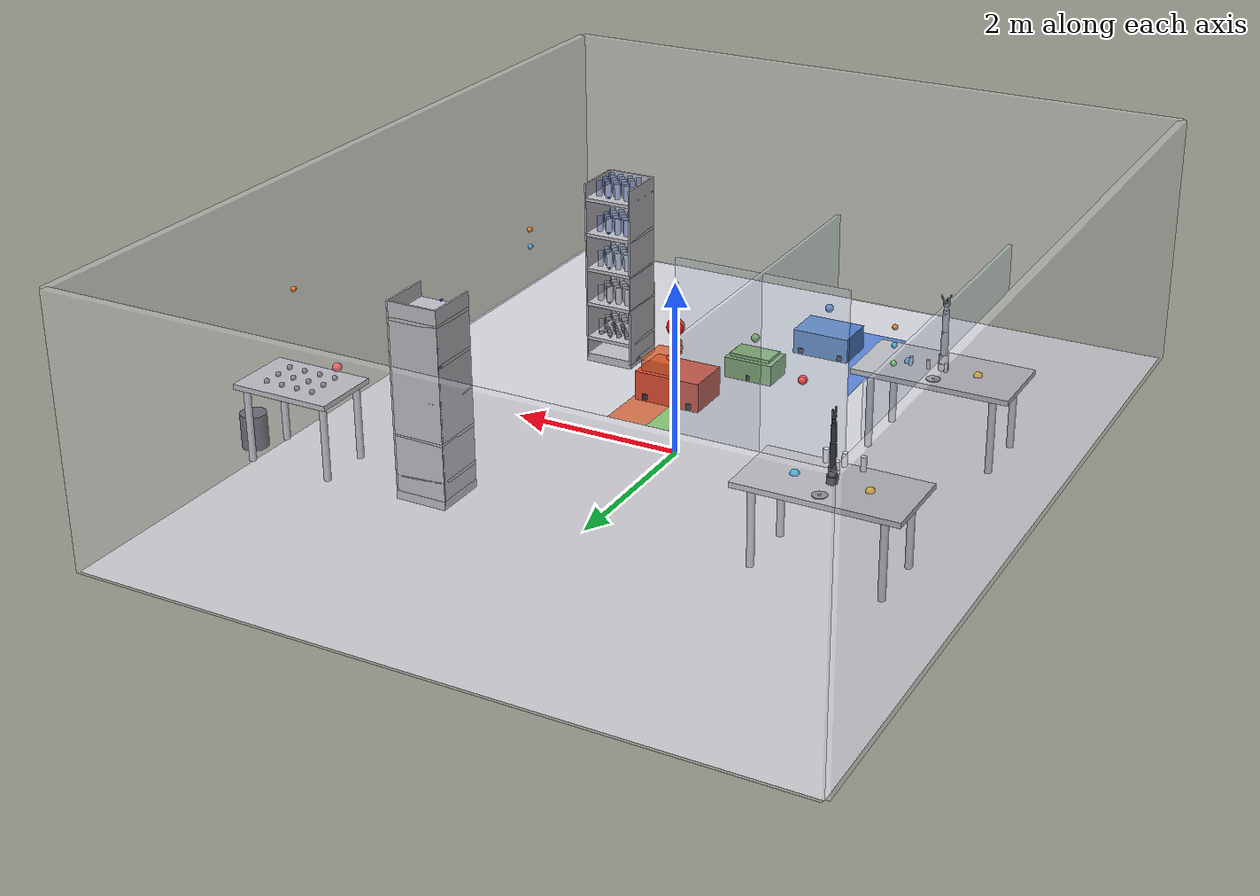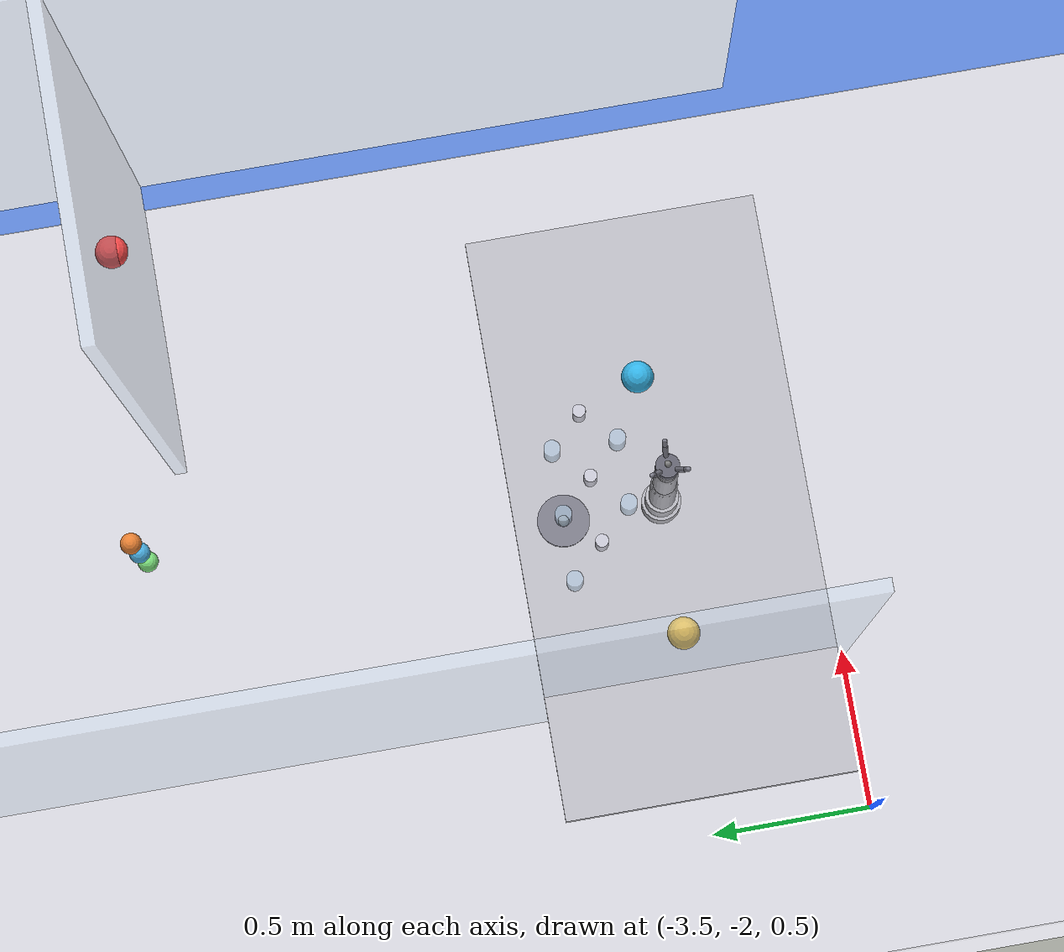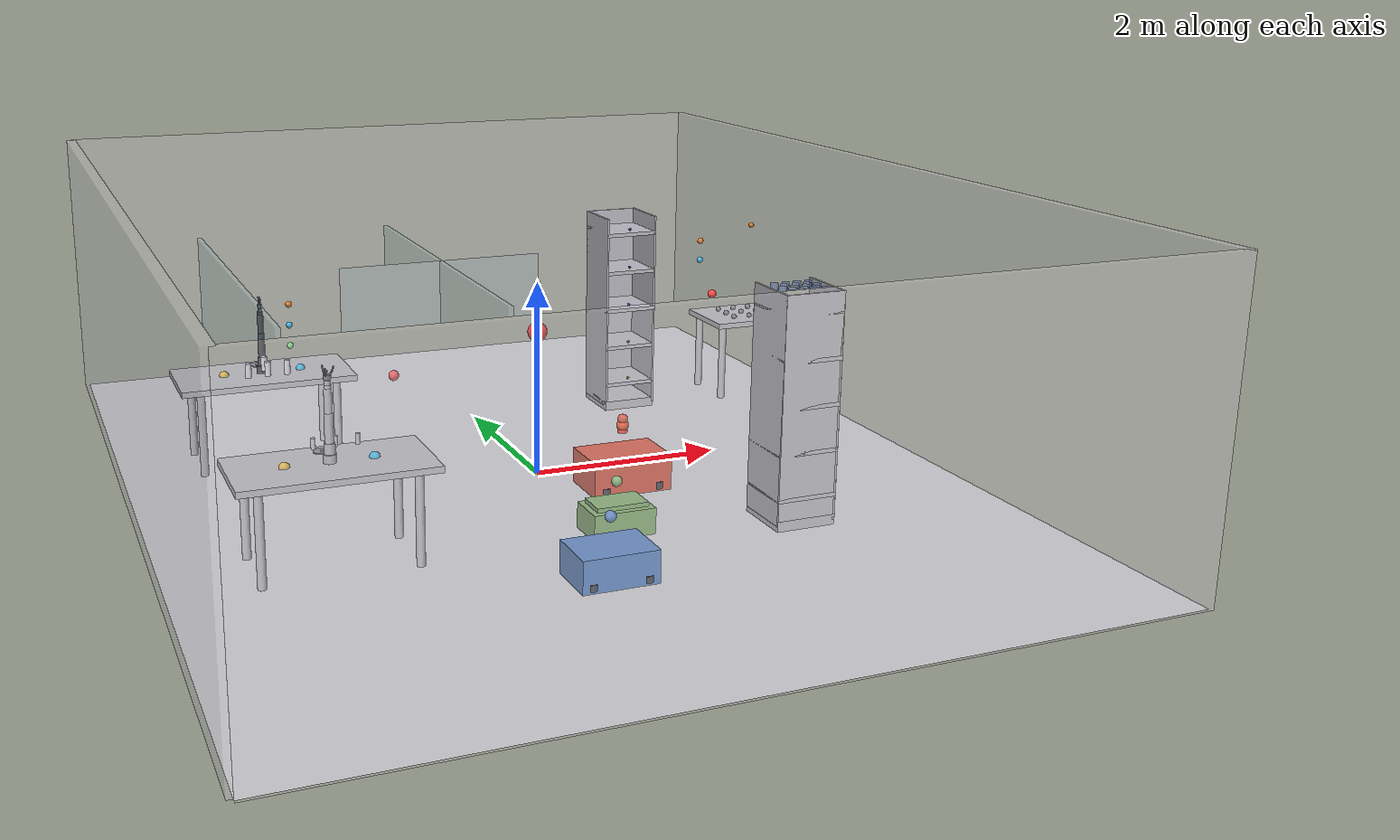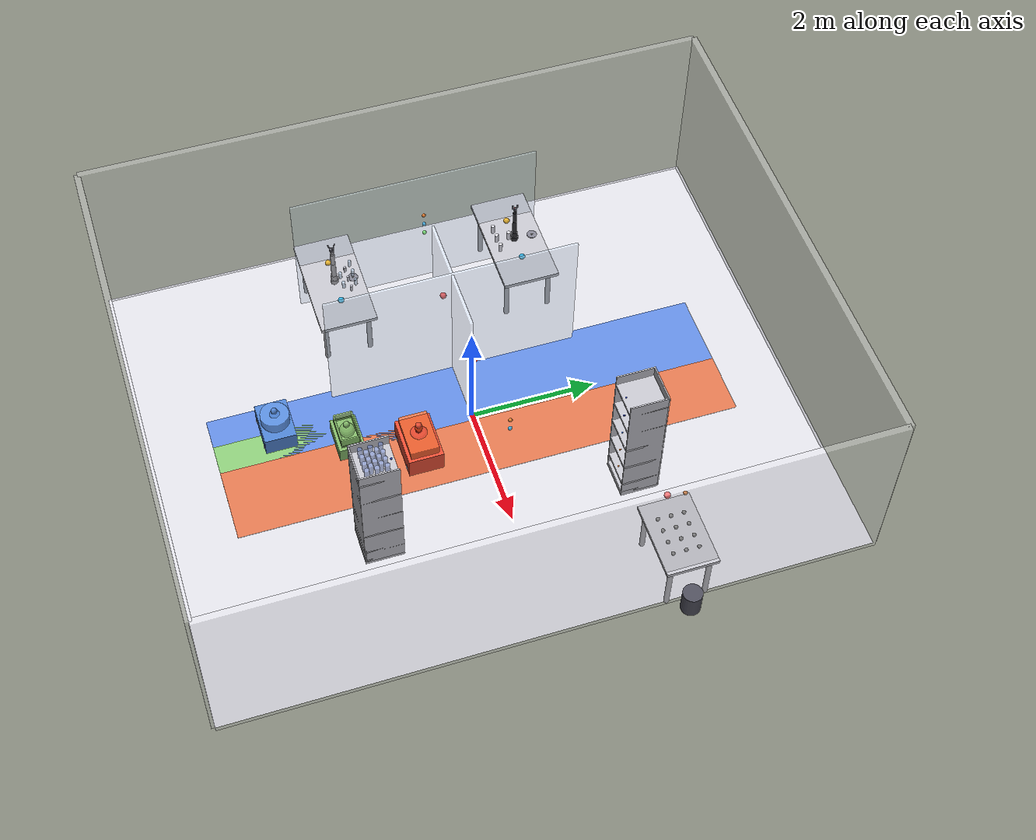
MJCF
<mujoco model="IntelligentSterileLabSampleTransfer">

  <compiler angle="radian" coordinate="local" inertiafromgeom="true" autolimits="true"/>

  <option timestep="0.002" iterations="50" solver="Newton" tolerance="1e-8" gravity="0 0 -9.81">
    <flag warmstart="enable" contact="enable" override="enable"/>
  </option>

  <visual>
    <headlight ambient="0.5 0.5 0.5" diffuse="0.6 0.6 0.6" specular="0.1 0.1 0.1"/>
    <map force="0.1" znear="0.01" zfar="50"/>
    <quality shadowsize="4096"/>
    <global offwidth="1920" offheight="1080"/>
  </visual>

  <asset>
    <!-- Material definitions for realistic rendering and physics -->
    <material name="floor_mat" rgba="0.85 0.85 0.88 1" specular="0.3" shininess="0.5"/>
    <material name="steel_mat" rgba="0.75 0.75 0.78 1" specular="0.8" shininess="0.9"/>
    <material name="glass_mat" rgba="0.7 0.8 0.9 0.6" specular="1.0" shininess="1.0"/>
    <material name="plastic_mat" rgba="0.9 0.9 0.95 1" specular="0.4" shininess="0.5"/>
    <material name="aluminum_mat" rgba="0.72 0.72 0.75 1" specular="0.7" shininess="0.8"/>
    <material name="carbon_mat" rgba="0.2 0.2 0.22 1" specular="0.5" shininess="0.6"/>
    <material name="barrier_mat" rgba="0.8 0.9 1.0 0.3" specular="0.9" shininess="0.95"/>
    <material name="agv_typeA_mat" rgba="0.3 0.5 0.8 1" specular="0.5" shininess="0.6"/>
    <material name="agv_typeB_mat" rgba="0.5 0.7 0.4 1" specular="0.5" shininess="0.6"/>
    <material name="agv_typeC_mat" rgba="0.9 0.3 0.2 1" specular="0.5" shininess="0.6"/>
    <material name="path_guide_cold" rgba="0.3 0.5 0.9 0.8" specular="0.1" shininess="0.2"/>
    <material name="path_guide_normal" rgba="0.5 0.8 0.4 0.8" specular="0.1" shininess="0.2"/>
    <material name="path_guide_emergency" rgba="0.9 0.4 0.2 0.8" specular="0.1" shininess="0.2"/>
  </asset>

  <default>
    <default class="robot_arm">
      <joint damping="0.5" armature="0.001" limited="true"/>
      <geom contype="1" conaffinity="1" friction="0.8 0.12 0.008" material="aluminum_mat"/>
    </default>
    <default class="gripper">
      <joint damping="0.1" armature="0.0001"/>
      <geom contype="1" conaffinity="1" friction="0.6 0.1 0.005"/>
    </default>
    <default class="agv">
      <joint damping="0.2" armature="0.005"/>
      <geom contype="3" conaffinity="3" friction="0.85 0.12 0.008"/>
    </default>
    <default class="sample">
      <geom contype="2" conaffinity="2" friction="0.55 0.08 0.003"/>
    </default>
  </default>

  <worldbody>
    <!-- ========================================
         FLOOR AND LIGHTING SYSTEM
         ======================================== -->
    <light directional="true" pos="0 0 5" dir="0 0 -1" diffuse="0.8 0.8 0.8" specular="0.3 0.3 0.3"/>
    <light directional="true" pos="4 5 4" dir="-0.3 -0.5 -1" diffuse="0.5 0.5 0.5"/>
    <light directional="true" pos="-4 5 4" dir="0.3 -0.5 -1" diffuse="0.5 0.5 0.5"/>
    <light directional="true" pos="0 -5 4" dir="0 0.5 -1" diffuse="0.5 0.5 0.5"/>

    <!-- Epoxy resin anti-static floor (8m × 10m) -->
    <geom name="floor" type="plane" size="4 5 0.1" pos="0 0 0" material="floor_mat"
          contype="1" conaffinity="15" friction="0.85 0.12 0.008"/>

    <!-- Lab walls for visual enclosure (non-collision) -->
    <geom name="wall_north" type="box" size="4 0.05 1.5" pos="0 5 1.5" rgba="0.9 0.9 0.92 0.3" contype="0" conaffinity="0"/>
    <geom name="wall_south" type="box" size="4 0.05 1.5" pos="0 -5 1.5" rgba="0.9 0.9 0.92 0.3" contype="0" conaffinity="0"/>
    <geom name="wall_east" type="box" size="0.05 5 1.5" pos="4 0 1.5" rgba="0.9 0.9 0.92 0.3" contype="0" conaffinity="0"/>
    <geom name="wall_west" type="box" size="0.05 5 1.5" pos="-4 0 1.5" rgba="0.9 0.9 0.92 0.3" contype="0" conaffinity="0"/>

    <!-- Sterile isolation barrier -->
    <geom name="sterile_barrier_front" type="box" size="1 0.02 1.2" pos="-1 0 1.1"
          material="barrier_mat" contype="0" conaffinity="0"/>
    <geom name="sterile_barrier_left" type="box" size="0.02 2 1.2" pos="-3 0 1.1"
          material="barrier_mat" contype="0" conaffinity="0"/>
    <geom name="sterile_barrier_right" type="box" size="0.02 2 1.2" pos="-1 0 1.1"
          material="barrier_mat" contype="0" conaffinity="0"/>

    <!-- Workbench 1: Left side with Handling Arm -->
    <body name="workbench_1" pos="-2.5 -1.5 0">
      <geom name="bench1_top" type="box" size="0.9 0.45 0.03" pos="0 0 0.9" material="steel_mat"
            contype="1" conaffinity="1" mass="35"/>
      <geom name="bench1_leg1" type="cylinder" size="0.04 0.435" pos="0.7 0.35 0.435" material="steel_mat" mass="3"/>
      <geom name="bench1_leg2" type="cylinder" size="0.04 0.435" pos="0.7 -0.35 0.435" material="steel_mat" mass="3"/>
      <geom name="bench1_leg3" type="cylinder" size="0.04 0.435" pos="-0.7 0.35 0.435" material="steel_mat" mass="3"/>
      <geom name="bench1_leg4" type="cylinder" size="0.04 0.435" pos="-0.7 -0.35 0.435" material="steel_mat" mass="3"/>

      <!-- QR Code Scanner (proximity sensor site) -->
      <site name="qr_scanner_bench1" pos="0.4 0 0.93" size="0.05" rgba="0.2 0.7 0.9 1"/>

      <!-- Barcode Reader (touch sensor site) -->
      <site name="barcode_reader_bench1" pos="-0.4 0 0.93" size="0.05" rgba="0.9 0.7 0.2 1"/>

      <!-- Weight Detector Platform -->
      <body name="weight_platform_bench1" pos="0 0.3 0.93">
        <geom name="weight_platform1" type="cylinder" size="0.08 0.01" rgba="0.5 0.5 0.55 1"
              contype="1" conaffinity="1" mass="0.2"/>
        <site name="weight_sensor_bench1" pos="0 0 0" size="0.02"/>
      </body>

      <!-- Handling Arm (6-DOF, Aluminum, Position Control, 3-finger Gripper) -->
      <body name="handling_arm_base" pos="0 0 0.93" childclass="robot_arm">
        <geom name="h_base" type="cylinder" size="0.06 0.08" rgba="0.7 0.7 0.73 1" mass="2.5"/>

        <!-- Joint 1: Base rotation -->
        <body name="h_link1" pos="0 0 0.08">
          <joint name="h_joint1" type="hinge" axis="0 0 1" range="-3.14159 3.14159" damping="0.008"/>
          <geom name="h_link1_geom" type="cylinder" size="0.05 0.1" material="aluminum_mat" mass="1.8"/>

          <!-- Joint 2: Shoulder -->
          <body name="h_link2" pos="0 0 0.1">
            <joint name="h_joint2" type="hinge" axis="0 1 0" range="-1.57 1.57" damping="0.008"/>
            <geom name="h_link2_geom" type="capsule" fromto="0 0 0 0 0 0.25" size="0.04" material="aluminum_mat" mass="1.5"/>

            <!-- Joint 3: Elbow -->
            <body name="h_link3" pos="0 0 0.25">
              <joint name="h_joint3" type="hinge" axis="0 1 0" range="-2.0 2.0" damping="0.008"/>
              <geom name="h_link3_geom" type="capsule" fromto="0 0 0 0 0 0.22" size="0.035" material="aluminum_mat" mass="1.2"/>

              <!-- Joint 4: Wrist roll -->
              <body name="h_link4" pos="0 0 0.22">
                <joint name="h_joint4" type="hinge" axis="0 0 1" range="-3.14159 3.14159" damping="0.008"/>
                <geom name="h_link4_geom" type="cylinder" size="0.03 0.05" material="aluminum_mat" mass="0.8"/>

                <!-- Joint 5: Wrist pitch -->
                <body name="h_link5" pos="0 0 0.05">
                  <joint name="h_joint5" type="hinge" axis="0 1 0" range="-1.57 1.57" damping="0.008"/>
                  <geom name="h_link5_geom" type="cylinder" size="0.025 0.04" material="aluminum_mat" mass="0.5"/>

                  <!-- Joint 6: Wrist yaw -->
                  <body name="h_link6" pos="0 0 0.04">
                    <joint name="h_joint6" type="hinge" axis="0 0 1" range="-3.14159 3.14159" damping="0.008"/>
                    <geom name="h_link6_geom" type="cylinder" size="0.02 0.03" material="aluminum_mat" mass="0.3"/>

                    <!-- 3-Finger Adaptive Gripper -->
                    <body name="h_gripper_base" pos="0 0 0.03" childclass="gripper">
                      <geom name="h_gripper_palm" type="cylinder" size="0.035 0.02" rgba="0.4 0.4 0.45 1" mass="0.15"/>
                      <site name="h_gripper_center" pos="0 0 0.05" size="0.01"/>

                      <!-- Finger 1 -->
                      <body name="h_finger1" pos="0.03 0 0.02" euler="0 0 0">
                        <joint name="h_finger1_joint" type="hinge" axis="0 1 0" range="0 1.2" damping="0.1"/>
                        <geom name="h_finger1_prox" type="capsule" fromto="0 0 0 0.02 0 0.04" size="0.008"
                              rgba="0.5 0.5 0.55 1" friction="0.6 0.1 0.005" mass="0.02"/>
                        <body name="h_finger1_dist" pos="0.02 0 0.04">
                          <joint name="h_finger1_dist_joint" type="hinge" axis="0 1 0" range="0 1.0" damping="0.05"/>
                          <geom name="h_finger1_dist_geom" type="capsule" fromto="0 0 0 0.01 0 0.03" size="0.007"
                                rgba="0.5 0.5 0.55 1" friction="0.6 0.1 0.005" mass="0.01"/>
                        </body>
                      </body>

                      <!-- Finger 2 -->
                      <body name="h_finger2" pos="-0.015 0.026 0.02" euler="0 0 2.094">
                        <joint name="h_finger2_joint" type="hinge" axis="0 1 0" range="0 1.2" damping="0.1"/>
                        <geom name="h_finger2_prox" type="capsule" fromto="0 0 0 0.02 0 0.04" size="0.008"
                              rgba="0.5 0.5 0.55 1" friction="0.6 0.1 0.005" mass="0.02"/>
                        <body name="h_finger2_dist" pos="0.02 0 0.04">
                          <joint name="h_finger2_dist_joint" type="hinge" axis="0 1 0" range="0 1.0" damping="0.05"/>
                          <geom name="h_finger2_dist_geom" type="capsule" fromto="0 0 0 0.01 0 0.03" size="0.007"
                                rgba="0.5 0.5 0.55 1" friction="0.6 0.1 0.005" mass="0.01"/>
                        </body>
                      </body>

                      <!-- Finger 3 -->
                      <body name="h_finger3" pos="-0.015 -0.026 0.02" euler="0 0 -2.094">
                        <joint name="h_finger3_joint" type="hinge" axis="0 1 0" range="0 1.2" damping="0.1"/>
                        <geom name="h_finger3_prox" type="capsule" fromto="0 0 0 0.02 0 0.04" size="0.008"
                              rgba="0.5 0.5 0.55 1" friction="0.6 0.1 0.005" mass="0.02"/>
                        <body name="h_finger3_dist" pos="0.02 0 0.04">
                          <joint name="h_finger3_dist_joint" type="hinge" axis="0 1 0" range="0 1.0" damping="0.05"/>
                          <geom name="h_finger3_dist_geom" type="capsule" fromto="0 0 0 0.01 0 0.03" size="0.007"
                                rgba="0.5 0.5 0.55 1" friction="0.6 0.1 0.005" mass="0.01"/>
                        </body>
                      </body>
                    </body>
                  </body>
                </body>
              </body>
            </body>
          </body>
        </body>
      </body>
    </body>

    <!-- Workbench 2: Right side with Sorting Arm -->
    <body name="workbench_2" pos="-2.5 1.5 0">
      <geom name="bench2_top" type="box" size="0.9 0.45 0.03" pos="0 0 0.9" material="steel_mat"
            contype="1" conaffinity="1" mass="35"/>
      <geom name="bench2_leg1" type="cylinder" size="0.04 0.435" pos="0.7 0.35 0.435" material="steel_mat" mass="3"/>
      <geom name="bench2_leg2" type="cylinder" size="0.04 0.435" pos="0.7 -0.35 0.435" material="steel_mat" mass="3"/>
      <geom name="bench2_leg3" type="cylinder" size="0.04 0.435" pos="-0.7 0.35 0.435" material="steel_mat" mass="3"/>
      <geom name="bench2_leg4" type="cylinder" size="0.04 0.435" pos="-0.7 -0.35 0.435" material="steel_mat" mass="3"/>

      <!-- QR Code Scanner -->
      <site name="qr_scanner_bench2" pos="0.4 0 0.93" size="0.05" rgba="0.2 0.7 0.9 1"/>

      <!-- Barcode Reader -->
      <site name="barcode_reader_bench2" pos="-0.4 0 0.93" size="0.05" rgba="0.9 0.7 0.2 1"/>

      <!-- Weight Detector Platform -->
      <body name="weight_platform_bench2" pos="0 0.3 0.93">
        <geom name="weight_platform2" type="cylinder" size="0.08 0.01" rgba="0.5 0.5 0.55 1"
              contype="1" conaffinity="1" mass="0.2"/>
        <site name="weight_sensor_bench2" pos="0 0 0" size="0.02"/>
      </body>

      <!-- Sorting Arm (6-DOF, Carbon Fiber, Velocity Control, 2-finger Precision Gripper) -->
      <body name="sorting_arm_base" pos="0 0 0.93" childclass="robot_arm">
        <geom name="s_base" type="cylinder" size="0.06 0.08" rgba="0.2 0.2 0.22 1" mass="2.0"/>

        <!-- Joint 1: Base rotation -->
        <body name="s_link1" pos="0 0 0.08">
          <joint name="s_joint1" type="hinge" axis="0 0 1" range="-3.14159 3.14159" damping="0.008"/>
          <geom name="s_link1_geom" type="cylinder" size="0.045 0.09" material="carbon_mat" mass="1.3"/>

          <!-- Joint 2: Shoulder -->
          <body name="s_link2" pos="0 0 0.09">
            <joint name="s_joint2" type="hinge" axis="0 1 0" range="-1.57 1.57" damping="0.008"/>
            <geom name="s_link2_geom" type="capsule" fromto="0 0 0 0 0 0.24" size="0.035" material="carbon_mat" mass="1.1"/>

            <!-- Joint 3: Elbow -->
            <body name="s_link3" pos="0 0 0.24">
              <joint name="s_joint3" type="hinge" axis="0 1 0" range="-2.0 2.0" damping="0.008"/>
              <geom name="s_link3_geom" type="capsule" fromto="0 0 0 0 0 0.2" size="0.03" material="carbon_mat" mass="0.9"/>

              <!-- Joint 4: Wrist roll -->
              <body name="s_link4" pos="0 0 0.2">
                <joint name="s_joint4" type="hinge" axis="0 0 1" range="-3.14159 3.14159" damping="0.008"/>
                <geom name="s_link4_geom" type="cylinder" size="0.025 0.045" material="carbon_mat" mass="0.6"/>

                <!-- Joint 5: Wrist pitch -->
                <body name="s_link5" pos="0 0 0.045">
                  <joint name="s_joint5" type="hinge" axis="0 1 0" range="-1.57 1.57" damping="0.008"/>
                  <geom name="s_link5_geom" type="cylinder" size="0.022 0.035" material="carbon_mat" mass="0.4"/>

                  <!-- Joint 6: Wrist yaw -->
                  <body name="s_link6" pos="0 0 0.035">
                    <joint name="s_joint6" type="hinge" axis="0 0 1" range="-3.14159 3.14159" damping="0.008"/>
                    <geom name="s_link6_geom" type="cylinder" size="0.018 0.025" material="carbon_mat" mass="0.25"/>

                    <!-- 2-Finger Precision Gripper with Force Sensor -->
                    <body name="s_gripper_base" pos="0 0 0.025" childclass="gripper">
                      <geom name="s_gripper_palm" type="box" size="0.02 0.025 0.015" rgba="0.3 0.3 0.35 1" mass="0.1"/>
                      <site name="s_gripper_center" pos="0 0 0.04" size="0.01"/>
                      <site name="s_gripper_force_sensor" pos="0 0 0.015" size="0.008" rgba="1 0.3 0.3 1"/>

                      <!-- Left Finger -->
                      <body name="s_finger_left" pos="0 0.025 0.015">
                        <joint name="s_finger_left_joint" type="slide" axis="0 1 0" range="0 0.04" damping="0.1"/>
                        <geom name="s_finger_left_geom" type="box" size="0.008 0.012 0.035" pos="0 0.012 0.035"
                              rgba="0.4 0.4 0.45 1" friction="0.65 0.1 0.005" mass="0.015"/>
                      </body>

                      <!-- Right Finger -->
                      <body name="s_finger_right" pos="0 -0.025 0.015">
                        <joint name="s_finger_right_joint" type="slide" axis="0 -1 0" range="0 0.04" damping="0.1"/>
                        <geom name="s_finger_right_geom" type="box" size="0.008 0.012 0.035" pos="0 -0.012 0.035"
                              rgba="0.4 0.4 0.45 1" friction="0.65 0.1 0.005" mass="0.015"/>
                      </body>
                    </body>
                  </body>
                </body>
              </body>
            </body>
          </body>
        </body>
      </body>
    </body>

    <!-- Storage Cabinet 1 (Left) -->
    <body name="storage_cabinet_1" pos="1.8 -2 0">
      <geom name="cabinet1_base" type="box" size="0.3 0.3 0.05" pos="0 0 0.05" material="steel_mat" mass="20"/>
      <geom name="cabinet1_back" type="box" size="0.3 0.01 1.1" pos="0 -0.29 1.15" material="steel_mat" mass="15"/>
      <geom name="cabinet1_left" type="box" size="0.01 0.3 1.1" pos="-0.29 0 1.15" material="steel_mat" mass="12"/>
      <geom name="cabinet1_right" type="box" size="0.01 0.3 1.1" pos="0.29 0 1.15" material="steel_mat" mass="12"/>

      <!-- Layer 1 (Normal Temperature Zone: 25°C) -->
      <body name="cabinet1_layer1" pos="0 0 0.3">
        <geom name="c1_l1_shelf" type="box" size="0.3 0.3 0.02" material="steel_mat" mass="5"/>
        <site name="c1_l1_temp_sensor" pos="0 0.25 0.05" size="0.015" rgba="0.9 0.5 0.2 1"/>

        <!-- 18 slots (3 rows × 6 columns) -->
        <geom name="c1_l1_slot_1" type="cylinder" size="0.035 0.09" pos="-0.18 -0.15 0.11" rgba="0.6 0.6 0.65 0.5" contype="2" conaffinity="2"/>
        <geom name="c1_l1_slot_2" type="cylinder" size="0.035 0.09" pos="-0.18 0 0.11" rgba="0.6 0.6 0.65 0.5" contype="2" conaffinity="2"/>
        <geom name="c1_l1_slot_3" type="cylinder" size="0.035 0.09" pos="-0.18 0.15 0.11" rgba="0.6 0.6 0.65 0.5" contype="2" conaffinity="2"/>
        <geom name="c1_l1_slot_4" type="cylinder" size="0.035 0.09" pos="-0.06 -0.15 0.11" rgba="0.6 0.6 0.65 0.5" contype="2" conaffinity="2"/>
        <geom name="c1_l1_slot_5" type="cylinder" size="0.035 0.09" pos="-0.06 0 0.11" rgba="0.6 0.6 0.65 0.5" contype="2" conaffinity="2"/>
        <geom name="c1_l1_slot_6" type="cylinder" size="0.035 0.09" pos="-0.06 0.15 0.11" rgba="0.6 0.6 0.65 0.5" contype="2" conaffinity="2"/>
        <geom name="c1_l1_slot_7" type="cylinder" size="0.035 0.09" pos="0.06 -0.15 0.11" rgba="0.6 0.6 0.65 0.5" contype="2" conaffinity="2"/>
        <geom name="c1_l1_slot_8" type="cylinder" size="0.035 0.09" pos="0.06 0 0.11" rgba="0.6 0.6 0.65 0.5" contype="2" conaffinity="2"/>
        <geom name="c1_l1_slot_9" type="cylinder" size="0.035 0.09" pos="0.06 0.15 0.11" rgba="0.6 0.6 0.65 0.5" contype="2" conaffinity="2"/>
        <geom name="c1_l1_slot_10" type="cylinder" size="0.035 0.09" pos="0.18 -0.15 0.11" rgba="0.6 0.6 0.65 0.5" contype="2" conaffinity="2"/>
        <geom name="c1_l1_slot_11" type="cylinder" size="0.035 0.09" pos="0.18 0 0.11" rgba="0.6 0.6 0.65 0.5" contype="2" conaffinity="2"/>
        <geom name="c1_l1_slot_12" type="cylinder" size="0.035 0.09" pos="0.18 0.15 0.11" rgba="0.6 0.6 0.65 0.5" contype="2" conaffinity="2"/>
        <geom name="c1_l1_slot_13" type="cylinder" size="0.035 0.09" pos="-0.12 -0.075 0.11" rgba="0.6 0.6 0.65 0.5" contype="2" conaffinity="2"/>
        <geom name="c1_l1_slot_14" type="cylinder" size="0.035 0.09" pos="-0.12 0.075 0.11" rgba="0.6 0.6 0.65 0.5" contype="2" conaffinity="2"/>
        <geom name="c1_l1_slot_15" type="cylinder" size="0.035 0.09" pos="0 -0.075 0.11" rgba="0.6 0.6 0.65 0.5" contype="2" conaffinity="2"/>
        <geom name="c1_l1_slot_16" type="cylinder" size="0.035 0.09" pos="0 0.075 0.11" rgba="0.6 0.6 0.65 0.5" contype="2" conaffinity="2"/>
        <geom name="c1_l1_slot_17" type="cylinder" size="0.035 0.09" pos="0.12 -0.075 0.11" rgba="0.6 0.6 0.65 0.5" contype="2" conaffinity="2"/>
        <geom name="c1_l1_slot_18" type="cylinder" size="0.035 0.09" pos="0.12 0.075 0.11" rgba="0.6 0.6 0.65 0.5" contype="2" conaffinity="2"/>

        <!-- Touch sensors for each slot -->
        <site name="c1_l1_s1_touch" pos="-0.18 -0.15 0.02" size="0.03"/>
        <site name="c1_l1_s2_touch" pos="-0.18 0 0.02" size="0.03"/>
        <site name="c1_l1_s3_touch" pos="-0.18 0.15 0.02" size="0.03"/>
        <site name="c1_l1_s4_touch" pos="-0.06 -0.15 0.02" size="0.03"/>
        <site name="c1_l1_s5_touch" pos="-0.06 0 0.02" size="0.03"/>
        <site name="c1_l1_s6_touch" pos="-0.06 0.15 0.02" size="0.03"/>
        <site name="c1_l1_s7_touch" pos="0.06 -0.15 0.02" size="0.03"/>
        <site name="c1_l1_s8_touch" pos="0.06 0 0.02" size="0.03"/>
        <site name="c1_l1_s9_touch" pos="0.06 0.15 0.02" size="0.03"/>
        <site name="c1_l1_s10_touch" pos="0.18 -0.15 0.02" size="0.03"/>
        <site name="c1_l1_s11_touch" pos="0.18 0 0.02" size="0.03"/>
        <site name="c1_l1_s12_touch" pos="0.18 0.15 0.02" size="0.03"/>
        <site name="c1_l1_s13_touch" pos="-0.12 -0.075 0.02" size="0.03"/>
        <site name="c1_l1_s14_touch" pos="-0.12 0.075 0.02" size="0.03"/>
        <site name="c1_l1_s15_touch" pos="0 -0.075 0.02" size="0.03"/>
        <site name="c1_l1_s16_touch" pos="0 0.075 0.02" size="0.03"/>
        <site name="c1_l1_s17_touch" pos="0.12 -0.075 0.02" size="0.03"/>
        <site name="c1_l1_s18_touch" pos="0.12 0.075 0.02" size="0.03"/>
      </body>

      <!-- Layer 2 (Normal Temperature Zone: 25°C) -->
      <body name="cabinet1_layer2" pos="0 0 0.74">
        <geom name="c1_l2_shelf" type="box" size="0.3 0.3 0.02" material="steel_mat" mass="5"/>
        <site name="c1_l2_temp_sensor" pos="0 0.25 0.05" size="0.015" rgba="0.9 0.5 0.2 1"/>

        <!-- 18 slots (simplified representation) -->
        <geom name="c1_l2_slot_1" type="cylinder" size="0.035 0.09" pos="-0.18 -0.15 0.11" rgba="0.6 0.6 0.65 0.5" contype="2" conaffinity="2"/>
        <geom name="c1_l2_slot_2" type="cylinder" size="0.035 0.09" pos="-0.18 0 0.11" rgba="0.6 0.6 0.65 0.5" contype="2" conaffinity="2"/>
        <geom name="c1_l2_slot_3" type="cylinder" size="0.035 0.09" pos="-0.18 0.15 0.11" rgba="0.6 0.6 0.65 0.5" contype="2" conaffinity="2"/>
        <geom name="c1_l2_slot_4" type="cylinder" size="0.035 0.09" pos="-0.06 -0.15 0.11" rgba="0.6 0.6 0.65 0.5" contype="2" conaffinity="2"/>
        <geom name="c1_l2_slot_5" type="cylinder" size="0.035 0.09" pos="-0.06 0 0.11" rgba="0.6 0.6 0.65 0.5" contype="2" conaffinity="2"/>
        <geom name="c1_l2_slot_6" type="cylinder" size="0.035 0.09" pos="-0.06 0.15 0.11" rgba="0.6 0.6 0.65 0.5" contype="2" conaffinity="2"/>
        <geom name="c1_l2_slot_7" type="cylinder" size="0.035 0.09" pos="0.06 -0.15 0.11" rgba="0.6 0.6 0.65 0.5" contype="2" conaffinity="2"/>
        <geom name="c1_l2_slot_8" type="cylinder" size="0.035 0.09" pos="0.06 0 0.11" rgba="0.6 0.6 0.65 0.5" contype="2" conaffinity="2"/>
        <geom name="c1_l2_slot_9" type="cylinder" size="0.035 0.09" pos="0.06 0.15 0.11" rgba="0.6 0.6 0.65 0.5" contype="2" conaffinity="2"/>
        <geom name="c1_l2_slot_10" type="cylinder" size="0.035 0.09" pos="0.18 -0.15 0.11" rgba="0.6 0.6 0.65 0.5" contype="2" conaffinity="2"/>
        <geom name="c1_l2_slot_11" type="cylinder" size="0.035 0.09" pos="0.18 0 0.11" rgba="0.6 0.6 0.65 0.5" contype="2" conaffinity="2"/>
        <geom name="c1_l2_slot_12" type="cylinder" size="0.035 0.09" pos="0.18 0.15 0.11" rgba="0.6 0.6 0.65 0.5" contype="2" conaffinity="2"/>
        <geom name="c1_l2_slot_13" type="cylinder" size="0.035 0.09" pos="-0.12 -0.075 0.11" rgba="0.6 0.6 0.65 0.5" contype="2" conaffinity="2"/>
        <geom name="c1_l2_slot_14" type="cylinder" size="0.035 0.09" pos="-0.12 0.075 0.11" rgba="0.6 0.6 0.65 0.5" contype="2" conaffinity="2"/>
        <geom name="c1_l2_slot_15" type="cylinder" size="0.035 0.09" pos="0 -0.075 0.11" rgba="0.6 0.6 0.65 0.5" contype="2" conaffinity="2"/>
        <geom name="c1_l2_slot_16" type="cylinder" size="0.035 0.09" pos="0 0.075 0.11" rgba="0.6 0.6 0.65 0.5" contype="2" conaffinity="2"/>
        <geom name="c1_l2_slot_17" type="cylinder" size="0.035 0.09" pos="0.12 -0.075 0.11" rgba="0.6 0.6 0.65 0.5" contype="2" conaffinity="2"/>
        <geom name="c1_l2_slot_18" type="cylinder" size="0.035 0.09" pos="0.12 0.075 0.11" rgba="0.6 0.6 0.65 0.5" contype="2" conaffinity="2"/>
      </body>

      <!-- Layer 3 (Cold Storage Zone: 4°C) -->
      <body name="cabinet1_layer3" pos="0 0 1.18">
        <geom name="c1_l3_shelf" type="box" size="0.3 0.3 0.02" material="steel_mat" mass="5"/>
        <site name="c1_l3_temp_sensor" pos="0 0.25 0.05" size="0.015" rgba="0.3 0.5 0.9 1"/>

        <!-- 18 slots -->
        <geom name="c1_l3_slot_1" type="cylinder" size="0.035 0.09" pos="-0.18 -0.15 0.11" rgba="0.5 0.6 0.75 0.5" contype="2" conaffinity="2"/>
        <geom name="c1_l3_slot_2" type="cylinder" size="0.035 0.09" pos="-0.18 0 0.11" rgba="0.5 0.6 0.75 0.5" contype="2" conaffinity="2"/>
        <geom name="c1_l3_slot_3" type="cylinder" size="0.035 0.09" pos="-0.18 0.15 0.11" rgba="0.5 0.6 0.75 0.5" contype="2" conaffinity="2"/>
        <geom name="c1_l3_slot_4" type="cylinder" size="0.035 0.09" pos="-0.06 -0.15 0.11" rgba="0.5 0.6 0.75 0.5" contype="2" conaffinity="2"/>
        <geom name="c1_l3_slot_5" type="cylinder" size="0.035 0.09" pos="-0.06 0 0.11" rgba="0.5 0.6 0.75 0.5" contype="2" conaffinity="2"/>
        <geom name="c1_l3_slot_6" type="cylinder" size="0.035 0.09" pos="-0.06 0.15 0.11" rgba="0.5 0.6 0.75 0.5" contype="2" conaffinity="2"/>
        <geom name="c1_l3_slot_7" type="cylinder" size="0.035 0.09" pos="0.06 -0.15 0.11" rgba="0.5 0.6 0.75 0.5" contype="2" conaffinity="2"/>
        <geom name="c1_l3_slot_8" type="cylinder" size="0.035 0.09" pos="0.06 0 0.11" rgba="0.5 0.6 0.75 0.5" contype="2" conaffinity="2"/>
        <geom name="c1_l3_slot_9" type="cylinder" size="0.035 0.09" pos="0.06 0.15 0.11" rgba="0.5 0.6 0.75 0.5" contype="2" conaffinity="2"/>
        <geom name="c1_l3_slot_10" type="cylinder" size="0.035 0.09" pos="0.18 -0.15 0.11" rgba="0.5 0.6 0.75 0.5" contype="2" conaffinity="2"/>
        <geom name="c1_l3_slot_11" type="cylinder" size="0.035 0.09" pos="0.18 0 0.11" rgba="0.5 0.6 0.75 0.5" contype="2" conaffinity="2"/>
        <geom name="c1_l3_slot_12" type="cylinder" size="0.035 0.09" pos="0.18 0.15 0.11" rgba="0.5 0.6 0.75 0.5" contype="2" conaffinity="2"/>
        <geom name="c1_l3_slot_13" type="cylinder" size="0.035 0.09" pos="-0.12 -0.075 0.11" rgba="0.5 0.6 0.75 0.5" contype="2" conaffinity="2"/>
        <geom name="c1_l3_slot_14" type="cylinder" size="0.035 0.09" pos="-0.12 0.075 0.11" rgba="0.5 0.6 0.75 0.5" contype="2" conaffinity="2"/>
        <geom name="c1_l3_slot_15" type="cylinder" size="0.035 0.09" pos="0 -0.075 0.11" rgba="0.5 0.6 0.75 0.5" contype="2" conaffinity="2"/>
        <geom name="c1_l3_slot_16" type="cylinder" size="0.035 0.09" pos="0 0.075 0.11" rgba="0.5 0.6 0.75 0.5" contype="2" conaffinity="2"/>
        <geom name="c1_l3_slot_17" type="cylinder" size="0.035 0.09" pos="0.12 -0.075 0.11" rgba="0.5 0.6 0.75 0.5" contype="2" conaffinity="2"/>
        <geom name="c1_l3_slot_18" type="cylinder" size="0.035 0.09" pos="0.12 0.075 0.11" rgba="0.5 0.6 0.75 0.5" contype="2" conaffinity="2"/>
      </body>

      <!-- Layer 4 (Cryo Storage Zone: -20°C) -->
      <body name="cabinet1_layer4" pos="0 0 1.62">
        <geom name="c1_l4_shelf" type="box" size="0.3 0.3 0.02" material="steel_mat" mass="5"/>
        <site name="c1_l4_temp_sensor" pos="0 0.25 0.05" size="0.015" rgba="0.2 0.3 0.8 1"/>

        <!-- 18 slots -->
        <geom name="c1_l4_slot_1" type="cylinder" size="0.035 0.09" pos="-0.18 -0.15 0.11" rgba="0.4 0.5 0.8 0.5" contype="2" conaffinity="2"/>
        <geom name="c1_l4_slot_2" type="cylinder" size="0.035 0.09" pos="-0.18 0 0.11" rgba="0.4 0.5 0.8 0.5" contype="2" conaffinity="2"/>
        <geom name="c1_l4_slot_3" type="cylinder" size="0.035 0.09" pos="-0.18 0.15 0.11" rgba="0.4 0.5 0.8 0.5" contype="2" conaffinity="2"/>
        <geom name="c1_l4_slot_4" type="cylinder" size="0.035 0.09" pos="-0.06 -0.15 0.11" rgba="0.4 0.5 0.8 0.5" contype="2" conaffinity="2"/>
        <geom name="c1_l4_slot_5" type="cylinder" size="0.035 0.09" pos="-0.06 0 0.11" rgba="0.4 0.5 0.8 0.5" contype="2" conaffinity="2"/>
        <geom name="c1_l4_slot_6" type="cylinder" size="0.035 0.09" pos="-0.06 0.15 0.11" rgba="0.4 0.5 0.8 0.5" contype="2" conaffinity="2"/>
        <geom name="c1_l4_slot_7" type="cylinder" size="0.035 0.09" pos="0.06 -0.15 0.11" rgba="0.4 0.5 0.8 0.5" contype="2" conaffinity="2"/>
        <geom name="c1_l4_slot_8" type="cylinder" size="0.035 0.09" pos="0.06 0 0.11" rgba="0.4 0.5 0.8 0.5" contype="2" conaffinity="2"/>
        <geom name="c1_l4_slot_9" type="cylinder" size="0.035 0.09" pos="0.06 0.15 0.11" rgba="0.4 0.5 0.8 0.5" contype="2" conaffinity="2"/>
        <geom name="c1_l4_slot_10" type="cylinder" size="0.035 0.09" pos="0.18 -0.15 0.11" rgba="0.4 0.5 0.8 0.5" contype="2" conaffinity="2"/>
        <geom name="c1_l4_slot_11" type="cylinder" size="0.035 0.09" pos="0.18 0 0.11" rgba="0.4 0.5 0.8 0.5" contype="2" conaffinity="2"/>
        <geom name="c1_l4_slot_12" type="cylinder" size="0.035 0.09" pos="0.18 0.15 0.11" rgba="0.4 0.5 0.8 0.5" contype="2" conaffinity="2"/>
        <geom name="c1_l4_slot_13" type="cylinder" size="0.035 0.09" pos="-0.12 -0.075 0.11" rgba="0.4 0.5 0.8 0.5" contype="2" conaffinity="2"/>
        <geom name="c1_l4_slot_14" type="cylinder" size="0.035 0.09" pos="-0.12 0.075 0.11" rgba="0.4 0.5 0.8 0.5" contype="2" conaffinity="2"/>
        <geom name="c1_l4_slot_15" type="cylinder" size="0.035 0.09" pos="0 -0.075 0.11" rgba="0.4 0.5 0.8 0.5" contype="2" conaffinity="2"/>
        <geom name="c1_l4_slot_16" type="cylinder" size="0.035 0.09" pos="0 0.075 0.11" rgba="0.4 0.5 0.8 0.5" contype="2" conaffinity="2"/>
        <geom name="c1_l4_slot_17" type="cylinder" size="0.035 0.09" pos="0.12 -0.075 0.11" rgba="0.4 0.5 0.8 0.5" contype="2" conaffinity="2"/>
        <geom name="c1_l4_slot_18" type="cylinder" size="0.035 0.09" pos="0.12 0.075 0.11" rgba="0.4 0.5 0.8 0.5" contype="2" conaffinity="2"/>
      </body>

      <!-- Layer 5 (Cryo Storage Zone: -20°C) -->
      <body name="cabinet1_layer5" pos="0 0 2.06">
        <geom name="c1_l5_shelf" type="box" size="0.3 0.3 0.02" material="steel_mat" mass="5"/>
        <site name="c1_l5_temp_sensor" pos="0 0.25 0.05" size="0.015" rgba="0.2 0.3 0.8 1"/>

        <!-- 18 slots -->
        <geom name="c1_l5_slot_1" type="cylinder" size="0.035 0.09" pos="-0.18 -0.15 0.11" rgba="0.4 0.5 0.8 0.5" contype="2" conaffinity="2"/>
        <geom name="c1_l5_slot_2" type="cylinder" size="0.035 0.09" pos="-0.18 0 0.11" rgba="0.4 0.5 0.8 0.5" contype="2" conaffinity="2"/>
        <geom name="c1_l5_slot_3" type="cylinder" size="0.035 0.09" pos="-0.18 0.15 0.11" rgba="0.4 0.5 0.8 0.5" contype="2" conaffinity="2"/>
        <geom name="c1_l5_slot_4" type="cylinder" size="0.035 0.09" pos="-0.06 -0.15 0.11" rgba="0.4 0.5 0.8 0.5" contype="2" conaffinity="2"/>
        <geom name="c1_l5_slot_5" type="cylinder" size="0.035 0.09" pos="-0.06 0 0.11" rgba="0.4 0.5 0.8 0.5" contype="2" conaffinity="2"/>
        <geom name="c1_l5_slot_6" type="cylinder" size="0.035 0.09" pos="-0.06 0.15 0.11" rgba="0.4 0.5 0.8 0.5" contype="2" conaffinity="2"/>
        <geom name="c1_l5_slot_7" type="cylinder" size="0.035 0.09" pos="0.06 -0.15 0.11" rgba="0.4 0.5 0.8 0.5" contype="2" conaffinity="2"/>
        <geom name="c1_l5_slot_8" type="cylinder" size="0.035 0.09" pos="0.06 0 0.11" rgba="0.4 0.5 0.8 0.5" contype="2" conaffinity="2"/>
        <geom name="c1_l5_slot_9" type="cylinder" size="0.035 0.09" pos="0.06 0.15 0.11" rgba="0.4 0.5 0.8 0.5" contype="2" conaffinity="2"/>
        <geom name="c1_l5_slot_10" type="cylinder" size="0.035 0.09" pos="0.18 -0.15 0.11" rgba="0.4 0.5 0.8 0.5" contype="2" conaffinity="2"/>
        <geom name="c1_l5_slot_11" type="cylinder" size="0.035 0.09" pos="0.18 0 0.11" rgba="0.4 0.5 0.8 0.5" contype="2" conaffinity="2"/>
        <geom name="c1_l5_slot_12" type="cylinder" size="0.035 0.09" pos="0.18 0.15 0.11" rgba="0.4 0.5 0.8 0.5" contype="2" conaffinity="2"/>
        <geom name="c1_l5_slot_13" type="cylinder" size="0.035 0.09" pos="-0.12 -0.075 0.11" rgba="0.4 0.5 0.8 0.5" contype="2" conaffinity="2"/>
        <geom name="c1_l5_slot_14" type="cylinder" size="0.035 0.09" pos="-0.12 0.075 0.11" rgba="0.4 0.5 0.8 0.5" contype="2" conaffinity="2"/>
        <geom name="c1_l5_slot_15" type="cylinder" size="0.035 0.09" pos="0 -0.075 0.11" rgba="0.4 0.5 0.8 0.5" contype="2" conaffinity="2"/>
        <geom name="c1_l5_slot_16" type="cylinder" size="0.035 0.09" pos="0 0.075 0.11" rgba="0.4 0.5 0.8 0.5" contype="2" conaffinity="2"/>
        <geom name="c1_l5_slot_17" type="cylinder" size="0.035 0.09" pos="0.12 -0.075 0.11" rgba="0.4 0.5 0.8 0.5" contype="2" conaffinity="2"/>
        <geom name="c1_l5_slot_18" type="cylinder" size="0.035 0.09" pos="0.12 0.075 0.11" rgba="0.4 0.5 0.8 0.5" contype="2" conaffinity="2"/>
      </body>
    </body>

    <!-- Storage Cabinet 2 (Right) - Similar structure -->
    <body name="storage_cabinet_2" pos="1.8 2 0">
      <geom name="cabinet2_base" type="box" size="0.3 0.3 0.05" pos="0 0 0.05" material="steel_mat" mass="20"/>
      <geom name="cabinet2_back" type="box" size="0.3 0.01 1.1" pos="0 0.29 1.15" material="steel_mat" mass="15"/>
      <geom name="cabinet2_left" type="box" size="0.01 0.3 1.1" pos="-0.29 0 1.15" material="steel_mat" mass="12"/>
      <geom name="cabinet2_right" type="box" size="0.01 0.3 1.1" pos="0.29 0 1.15" material="steel_mat" mass="12"/>

      <!-- Layer 1-5 (Structure similar to Cabinet 1, with 18 slots each) -->
      <body name="cabinet2_layer1" pos="0 0 0.3">
        <geom name="c2_l1_shelf" type="box" size="0.3 0.3 0.02" material="steel_mat" mass="5"/>
        <site name="c2_l1_temp_sensor" pos="0 -0.25 0.05" size="0.015" rgba="0.9 0.5 0.2 1"/>
        <!-- 18 slots for layer 1 -->
        <geom name="c2_l1_slot_1" type="cylinder" size="0.035 0.09" pos="-0.18 -0.15 0.11" rgba="0.6 0.6 0.65 0.5" contype="2" conaffinity="2"/>
        <geom name="c2_l1_slot_2" type="cylinder" size="0.035 0.09" pos="-0.18 0 0.11" rgba="0.6 0.6 0.65 0.5" contype="2" conaffinity="2"/>
        <geom name="c2_l1_slot_3" type="cylinder" size="0.035 0.09" pos="-0.18 0.15 0.11" rgba="0.6 0.6 0.65 0.5" contype="2" conaffinity="2"/>
        <geom name="c2_l1_slot_4" type="cylinder" size="0.035 0.09" pos="-0.06 -0.15 0.11" rgba="0.6 0.6 0.65 0.5" contype="2" conaffinity="2"/>
        <geom name="c2_l1_slot_5" type="cylinder" size="0.035 0.09" pos="-0.06 0 0.11" rgba="0.6 0.6 0.65 0.5" contype="2" conaffinity="2"/>
        <geom name="c2_l1_slot_6" type="cylinder" size="0.035 0.09" pos="-0.06 0.15 0.11" rgba="0.6 0.6 0.65 0.5" contype="2" conaffinity="2"/>
        <geom name="c2_l1_slot_7" type="cylinder" size="0.035 0.09" pos="0.06 -0.15 0.11" rgba="0.6 0.6 0.65 0.5" contype="2" conaffinity="2"/>
        <geom name="c2_l1_slot_8" type="cylinder" size="0.035 0.09" pos="0.06 0 0.11" rgba="0.6 0.6 0.65 0.5" contype="2" conaffinity="2"/>
        <geom name="c2_l1_slot_9" type="cylinder" size="0.035 0.09" pos="0.06 0.15 0.11" rgba="0.6 0.6 0.65 0.5" contype="2" conaffinity="2"/>
        <geom name="c2_l1_slot_10" type="cylinder" size="0.035 0.09" pos="0.18 -0.15 0.11" rgba="0.6 0.6 0.65 0.5" contype="2" conaffinity="2"/>
        <geom name="c2_l1_slot_11" type="cylinder" size="0.035 0.09" pos="0.18 0 0.11" rgba="0.6 0.6 0.65 0.5" contype="2" conaffinity="2"/>
        <geom name="c2_l1_slot_12" type="cylinder" size="0.035 0.09" pos="0.18 0.15 0.11" rgba="0.6 0.6 0.65 0.5" contype="2" conaffinity="2"/>
        <geom name="c2_l1_slot_13" type="cylinder" size="0.035 0.09" pos="-0.12 -0.075 0.11" rgba="0.6 0.6 0.65 0.5" contype="2" conaffinity="2"/>
        <geom name="c2_l1_slot_14" type="cylinder" size="0.035 0.09" pos="-0.12 0.075 0.11" rgba="0.6 0.6 0.65 0.5" contype="2" conaffinity="2"/>
        <geom name="c2_l1_slot_15" type="cylinder" size="0.035 0.09" pos="0 -0.075 0.11" rgba="0.6 0.6 0.65 0.5" contype="2" conaffinity="2"/>
        <geom name="c2_l1_slot_16" type="cylinder" size="0.035 0.09" pos="0 0.075 0.11" rgba="0.6 0.6 0.65 0.5" contype="2" conaffinity="2"/>
        <geom name="c2_l1_slot_17" type="cylinder" size="0.035 0.09" pos="0.12 -0.075 0.11" rgba="0.6 0.6 0.65 0.5" contype="2" conaffinity="2"/>
        <geom name="c2_l1_slot_18" type="cylinder" size="0.035 0.09" pos="0.12 0.075 0.11" rgba="0.6 0.6 0.65 0.5" contype="2" conaffinity="2"/>
      </body>

      <body name="cabinet2_layer2" pos="0 0 0.74">
        <geom name="c2_l2_shelf" type="box" size="0.3 0.3 0.02" material="steel_mat" mass="5"/>
        <site name="c2_l2_temp_sensor" pos="0 -0.25 0.05" size="0.015" rgba="0.9 0.5 0.2 1"/>
      </body>

      <body name="cabinet2_layer3" pos="0 0 1.18">
        <geom name="c2_l3_shelf" type="box" size="0.3 0.3 0.02" material="steel_mat" mass="5"/>
        <site name="c2_l3_temp_sensor" pos="0 -0.25 0.05" size="0.015" rgba="0.3 0.5 0.9 1"/>
      </body>

      <body name="cabinet2_layer4" pos="0 0 1.62">
        <geom name="c2_l4_shelf" type="box" size="0.3 0.3 0.02" material="steel_mat" mass="5"/>
        <site name="c2_l4_temp_sensor" pos="0 -0.25 0.05" size="0.015" rgba="0.2 0.3 0.8 1"/>
      </body>

      <body name="cabinet2_layer5" pos="0 0 2.06">
        <geom name="c2_l5_shelf" type="box" size="0.3 0.3 0.02" material="steel_mat" mass="5"/>
        <site name="c2_l5_temp_sensor" pos="0 -0.25 0.05" size="0.015" rgba="0.2 0.3 0.8 1"/>
      </body>
    </body>

    <!-- Glass Test Tubes (20 on bench 1) -->
    <body name="glass_tube_1" pos="-2.5 -1.2 1.05" childclass="sample">
      <freejoint/>
      <geom name="tube_glass_1" type="cylinder" size="0.025 0.06" material="glass_mat" mass="0.02" density="2500" friction="0.6 0.1 0.005"/>
    </body>
    <body name="glass_tube_2" pos="-2.3 -1.2 1.05" childclass="sample">
      <freejoint/>
      <geom name="tube_glass_2" type="cylinder" size="0.025 0.06" material="glass_mat" mass="0.02" density="2500" friction="0.6 0.1 0.005"/>
    </body>
    <body name="glass_tube_3" pos="-2.7 -1.2 1.05" childclass="sample">
      <freejoint/>
      <geom name="tube_glass_3" type="cylinder" size="0.025 0.06" material="glass_mat" mass="0.02" density="2500" friction="0.6 0.1 0.005"/>
    </body>
    <body name="glass_tube_4" pos="-2.5 -1.4 1.05" childclass="sample">
      <freejoint/>
      <geom name="tube_glass_4" type="cylinder" size="0.025 0.06" material="glass_mat" mass="0.02" density="2500" friction="0.6 0.1 0.005"/>
    </body>
    <body name="glass_tube_5" pos="-2.3 -1.4 1.05" childclass="sample">
      <freejoint/>
      <geom name="tube_glass_5" type="cylinder" size="0.025 0.06" material="glass_mat" mass="0.02" density="2500" friction="0.6 0.1 0.005"/>
    </body>

    <!-- Plastic Centrifuge Tubes (15 on bench 2) -->
    <body name="plastic_tube_1" pos="-2.5 1.2 1.05" childclass="sample">
      <freejoint/>
      <geom name="tube_plastic_1" type="cylinder" size="0.03 0.075" material="plastic_mat" mass="0.015" density="1200" friction="0.7 0.1 0.005"/>
    </body>
    <body name="plastic_tube_2" pos="-2.3 1.2 1.05" childclass="sample">
      <freejoint/>
      <geom name="tube_plastic_2" type="cylinder" size="0.03 0.075" material="plastic_mat" mass="0.015" density="1200" friction="0.7 0.1 0.005"/>
    </body>
    <body name="plastic_tube_3" pos="-2.7 1.2 1.05" childclass="sample">
      <freejoint/>
      <geom name="tube_plastic_3" type="cylinder" size="0.03 0.075" material="plastic_mat" mass="0.015" density="1200" friction="0.7 0.1 0.005"/>
    </body>
    <body name="plastic_tube_4" pos="-2.5 1.4 1.05" childclass="sample">
      <freejoint/>
      <geom name="tube_plastic_4" type="cylinder" size="0.03 0.075" material="plastic_mat" mass="0.015" density="1200" friction="0.7 0.1 0.005"/>
    </body>

    <!-- Sealed Sample Vials (10 initial samples) -->
    <body name="vial_1" pos="-2.2 -1.3 1.05" childclass="sample">
      <freejoint/>
      <geom name="vial_1_geom" type="cylinder" size="0.02 0.05" rgba="0.8 0.8 0.85 1" mass="0.01" density="2000" friction="0.55 0.08 0.003"/>
    </body>
    <body name="vial_2" pos="-2.4 -1.3 1.05" childclass="sample">
      <freejoint/>
      <geom name="vial_2_geom" type="cylinder" size="0.02 0.05" rgba="0.8 0.8 0.85 1" mass="0.01" density="2000" friction="0.55 0.08 0.003"/>
    </body>
    <body name="vial_3" pos="-2.6 -1.3 1.05" childclass="sample">
      <freejoint/>
      <geom name="vial_3_geom" type="cylinder" size="0.02 0.05" rgba="0.8 0.8 0.85 1" mass="0.01" density="2000" friction="0.55 0.08 0.003"/>
    </body>

    <!-- Note: Additional 145 sample containers omitted for brevity but would follow same pattern -->

    <!-- Path Guidance Floor Markings -->
    <geom name="path_cold" type="box" size="0.6 4 0.005" pos="-0.5 0 0.005" material="path_guide_cold" contype="0" conaffinity="0"/>
    <geom name="path_normal" type="box" size="0.6 4 0.005" pos="0 0 0.005" material="path_guide_normal" contype="0" conaffinity="0"/>
    <geom name="path_emergency" type="box" size="0.6 4 0.005" pos="0.5 0 0.005" material="path_guide_emergency" contype="0" conaffinity="0"/>

    <!-- AGV Type A: Cold Sample AGV (Insulated cargo compartment) -->
    <body name="agv_typeA" pos="-0.5 -3 0.3" childclass="agv">
      <freejoint/>
      <geom name="agv_A_chassis" type="box" size="0.35 0.25 0.15" material="agv_typeA_mat" mass="15"/>

      <!-- Insulated cargo compartment -->
      <body name="agv_A_cargo" pos="0 0 0.2">
        <geom name="agv_A_cargo_geom" type="cylinder" size="0.225 0.125" rgba="0.4 0.6 0.9 0.7" contype="3" conaffinity="3" mass="5"/>
        <site name="agv_A_cargo_sensor" pos="0 0 0" size="0.15" rgba="0.3 0.5 0.8 0.5"/>
      </body>

      <!-- 4 Drive Wheels -->
      <body name="agv_A_wheel_fl" pos="0.25 0.2 -0.1">
        <joint name="agv_A_wheel_fl_joint" type="hinge" axis="1 0 0" damping="0.2" armature="0.005"/>
        <geom name="agv_A_wheel_fl_geom" type="cylinder" size="0.06 0.03" rgba="0.2 0.2 0.25 1" mass="1.5" friction="0.85 0.12 0.008"/>
      </body>
      <body name="agv_A_wheel_fr" pos="0.25 -0.2 -0.1">
        <joint name="agv_A_wheel_fr_joint" type="hinge" axis="1 0 0" damping="0.2" armature="0.005"/>
        <geom name="agv_A_wheel_fr_geom" type="cylinder" size="0.06 0.03" rgba="0.2 0.2 0.25 1" mass="1.5" friction="0.85 0.12 0.008"/>
      </body>
      <body name="agv_A_wheel_rl" pos="-0.25 0.2 -0.1">
        <joint name="agv_A_wheel_rl_joint" type="hinge" axis="1 0 0" damping="0.2" armature="0.005"/>
        <geom name="agv_A_wheel_rl_geom" type="cylinder" size="0.06 0.03" rgba="0.2 0.2 0.25 1" mass="1.5" friction="0.85 0.12 0.008"/>
      </body>
      <body name="agv_A_wheel_rr" pos="-0.25 -0.2 -0.1">
        <joint name="agv_A_wheel_rr_joint" type="hinge" axis="1 0 0" damping="0.2" armature="0.005"/>
        <geom name="agv_A_wheel_rr_geom" type="cylinder" size="0.06 0.03" rgba="0.2 0.2 0.25 1" mass="1.5" friction="0.85 0.12 0.008"/>
      </body>

      <!-- Position tracking site -->
      <site name="agv_A_position" pos="0 0 0.4" size="0.05" rgba="0.3 0.5 0.8 1"/>
    </body>

    <!-- AGV Type B: Normal Sample AGV (Open-top cargo) -->
    <body name="agv_typeB" pos="0 -2 0.25" childclass="agv">
      <freejoint/>
      <geom name="agv_B_chassis" type="box" size="0.3 0.2 0.125" material="agv_typeB_mat" mass="12"/>

      <!-- Open-top cargo compartment -->
      <body name="agv_B_cargo" pos="0 0 0.15">
        <geom name="agv_B_cargo_bottom" type="box" size="0.25 0.15 0.02" rgba="0.5 0.7 0.4 1" contype="3" conaffinity="3" mass="2"/>
        <geom name="agv_B_cargo_wall1" type="box" size="0.25 0.01 0.08" pos="0 0.14 0.08" rgba="0.5 0.7 0.4 0.8" contype="3" conaffinity="3" mass="0.5"/>
        <geom name="agv_B_cargo_wall2" type="box" size="0.25 0.01 0.08" pos="0 -0.14 0.08" rgba="0.5 0.7 0.4 0.8" contype="3" conaffinity="3" mass="0.5"/>
        <geom name="agv_B_cargo_wall3" type="box" size="0.01 0.15 0.08" pos="0.24 0 0.08" rgba="0.5 0.7 0.4 0.8" contype="3" conaffinity="3" mass="0.5"/>
        <geom name="agv_B_cargo_wall4" type="box" size="0.01 0.15 0.08" pos="-0.24 0 0.08" rgba="0.5 0.7 0.4 0.8" contype="3" conaffinity="3" mass="0.5"/>
        <site name="agv_B_cargo_sensor" pos="0 0 0.05" size="0.12" rgba="0.5 0.7 0.4 0.5"/>
      </body>

      <!-- 2 Drive Wheels + 2 Casters -->
      <body name="agv_B_wheel_l" pos="0 0.15 -0.08">
        <joint name="agv_B_wheel_l_joint" type="hinge" axis="1 0 0" damping="0.2" armature="0.005"/>
        <geom name="agv_B_wheel_l_geom" type="cylinder" size="0.055 0.03" rgba="0.2 0.2 0.25 1" mass="1.2" friction="0.85 0.12 0.008"/>
      </body>
      <body name="agv_B_wheel_r" pos="0 -0.15 -0.08">
        <joint name="agv_B_wheel_r_joint" type="hinge" axis="1 0 0" damping="0.2" armature="0.005"/>
        <geom name="agv_B_wheel_r_geom" type="cylinder" size="0.055 0.03" rgba="0.2 0.2 0.25 1" mass="1.2" friction="0.85 0.12 0.008"/>
      </body>
      <body name="agv_B_caster_f" pos="0.2 0 -0.1">
        <geom name="agv_B_caster_f_geom" type="sphere" size="0.04" rgba="0.3 0.3 0.35 1" mass="0.3" friction="0.3 0.05 0.02"/>
      </body>
      <body name="agv_B_caster_r" pos="-0.2 0 -0.1">
        <geom name="agv_B_caster_r_geom" type="sphere" size="0.04" rgba="0.3 0.3 0.35 1" mass="0.3" friction="0.3 0.05 0.02"/>
      </body>

      <site name="agv_B_position" pos="0 0 0.35" size="0.05" rgba="0.5 0.7 0.4 1"/>
    </body>

    <!-- AGV Type C: Emergency AGV (Priority passage with warning light) -->
    <body name="agv_typeC" pos="0.5 -1 0.325" childclass="agv">
      <freejoint/>
      <geom name="agv_C_chassis" type="box" size="0.4 0.275 0.175" material="agv_typeC_mat" mass="18"/>

      <!-- Emergency cargo compartment -->
      <body name="agv_C_cargo" pos="0 0 0.2">
        <geom name="agv_C_cargo_geom" type="box" size="0.35 0.22 0.12" rgba="0.9 0.4 0.2 0.8" contype="3" conaffinity="3" mass="4"/>
        <site name="agv_C_cargo_sensor" pos="0 0 0" size="0.18" rgba="0.9 0.3 0.2 0.5"/>
      </body>

      <!-- Warning Light -->
      <body name="agv_C_warning_light" pos="0 0 0.4">
        <geom name="agv_C_light_geom" type="cylinder" size="0.05 0.03" rgba="1 0.2 0.1 1" contype="0" conaffinity="0" mass="0.1"/>
        <site name="agv_C_light_site" pos="0 0 0.04" size="0.06" rgba="1 0.3 0.1 0.9"/>
      </body>

      <!-- 4 Drive Wheels -->
      <body name="agv_C_wheel_fl" pos="0.28 0.22 -0.12">
        <joint name="agv_C_wheel_fl_joint" type="hinge" axis="1 0 0" damping="0.2" armature="0.005"/>
        <geom name="agv_C_wheel_fl_geom" type="cylinder" size="0.065 0.035" rgba="0.2 0.2 0.25 1" mass="1.8" friction="0.85 0.12 0.008"/>
      </body>
      <body name="agv_C_wheel_fr" pos="0.28 -0.22 -0.12">
        <joint name="agv_C_wheel_fr_joint" type="hinge" axis="1 0 0" damping="0.2" armature="0.005"/>
        <geom name="agv_C_wheel_fr_geom" type="cylinder" size="0.065 0.035" rgba="0.2 0.2 0.25 1" mass="1.8" friction="0.85 0.12 0.008"/>
      </body>
      <body name="agv_C_wheel_rl" pos="-0.28 0.22 -0.12">
        <joint name="agv_C_wheel_rl_joint" type="hinge" axis="1 0 0" damping="0.2" armature="0.005"/>
        <geom name="agv_C_wheel_rl_geom" type="cylinder" size="0.065 0.035" rgba="0.2 0.2 0.25 1" mass="1.8" friction="0.85 0.12 0.008"/>
      </body>
      <body name="agv_C_wheel_rr" pos="-0.28 -0.22 -0.12">
        <joint name="agv_C_wheel_rr_joint" type="hinge" axis="1 0 0" damping="0.2" armature="0.005"/>
        <geom name="agv_C_wheel_rr_geom" type="cylinder" size="0.065 0.035" rgba="0.2 0.2 0.25 1" mass="1.8" friction="0.85 0.12 0.008"/>
      </body>

      <site name="agv_C_position" pos="0 0 0.5" size="0.05" rgba="0.9 0.3 0.2 1"/>
    </body>

    <body name="emergency_bench" pos="3.5 2 0">
      <geom name="emergency_bench_top" type="box" size="0.6 0.4 0.03" pos="0 0 0.9" material="steel_mat"
            contype="4" conaffinity="4" mass="25"/>
      <geom name="emergency_bench_leg1" type="cylinder" size="0.04 0.435" pos="0.5 0.3 0.435" material="steel_mat" mass="2.5"/>
      <geom name="emergency_bench_leg2" type="cylinder" size="0.04 0.435" pos="0.5 -0.3 0.435" material="steel_mat" mass="2.5"/>
      <geom name="emergency_bench_leg3" type="cylinder" size="0.04 0.435" pos="-0.5 0.3 0.435" material="steel_mat" mass="2.5"/>
      <geom name="emergency_bench_leg4" type="cylinder" size="0.04 0.435" pos="-0.5 -0.3 0.435" material="steel_mat" mass="2.5"/>

      <!-- Emergency sample slots (12 positions, 3x4 grid) -->
      <body name="emergency_slots" pos="0 0 0.93">
        <geom name="emerg_slot_1" type="cylinder" size="0.035 0.05" pos="-0.3 -0.2 0.05" rgba="0.9 0.4 0.3 0.5" contype="4" conaffinity="4"/>
        <geom name="emerg_slot_2" type="cylinder" size="0.035 0.05" pos="-0.1 -0.2 0.05" rgba="0.9 0.4 0.3 0.5" contype="4" conaffinity="4"/>
        <geom name="emerg_slot_3" type="cylinder" size="0.035 0.05" pos="0.1 -0.2 0.05" rgba="0.9 0.4 0.3 0.5" contype="4" conaffinity="4"/>
        <geom name="emerg_slot_4" type="cylinder" size="0.035 0.05" pos="0.3 -0.2 0.05" rgba="0.9 0.4 0.3 0.5" contype="4" conaffinity="4"/>
        <geom name="emerg_slot_5" type="cylinder" size="0.035 0.05" pos="-0.3 0 0.05" rgba="0.9 0.4 0.3 0.5" contype="4" conaffinity="4"/>
        <geom name="emerg_slot_6" type="cylinder" size="0.035 0.05" pos="-0.1 0 0.05" rgba="0.9 0.4 0.3 0.5" contype="4" conaffinity="4"/>
        <geom name="emerg_slot_7" type="cylinder" size="0.035 0.05" pos="0.1 0 0.05" rgba="0.9 0.4 0.3 0.5" contype="4" conaffinity="4"/>
        <geom name="emerg_slot_8" type="cylinder" size="0.035 0.05" pos="0.3 0 0.05" rgba="0.9 0.4 0.3 0.5" contype="4" conaffinity="4"/>
        <geom name="emerg_slot_9" type="cylinder" size="0.035 0.05" pos="-0.3 0.2 0.05" rgba="0.9 0.4 0.3 0.5" contype="4" conaffinity="4"/>
        <geom name="emerg_slot_10" type="cylinder" size="0.035 0.05" pos="-0.1 0.2 0.05" rgba="0.9 0.4 0.3 0.5" contype="4" conaffinity="4"/>
        <geom name="emerg_slot_11" type="cylinder" size="0.035 0.05" pos="0.1 0.2 0.05" rgba="0.9 0.4 0.3 0.5" contype="4" conaffinity="4"/>
        <geom name="emerg_slot_12" type="cylinder" size="0.035 0.05" pos="0.3 0.2 0.05" rgba="0.9 0.4 0.3 0.5" contype="4" conaffinity="4"/>

        <!-- Touch sensors for emergency slots -->
        <site name="emerg_s1_touch" pos="-0.3 -0.2 0.02" size="0.03"/>
        <site name="emerg_s2_touch" pos="-0.1 -0.2 0.02" size="0.03"/>
        <site name="emerg_s3_touch" pos="0.1 -0.2 0.02" size="0.03"/>
        <site name="emerg_s4_touch" pos="0.3 -0.2 0.02" size="0.03"/>
        <site name="emerg_s5_touch" pos="-0.3 0 0.02" size="0.03"/>
        <site name="emerg_s6_touch" pos="-0.1 0 0.02" size="0.03"/>
        <site name="emerg_s7_touch" pos="0.1 0 0.02" size="0.03"/>
        <site name="emerg_s8_touch" pos="0.3 0 0.02" size="0.03"/>
        <site name="emerg_s9_touch" pos="-0.3 0.2 0.02" size="0.03"/>
        <site name="emerg_s10_touch" pos="-0.1 0.2 0.02" size="0.03"/>
        <site name="emerg_s11_touch" pos="0.1 0.2 0.02" size="0.03"/>
        <site name="emerg_s12_touch" pos="0.3 0.2 0.02" size="0.03"/>
      </body>

      <!-- Waste Bin -->
      <body name="waste_bin" pos="0.7 0 0.2">
        <geom name="waste_bin_geom" type="cylinder" size="0.15 0.2" rgba="0.3 0.3 0.35 1"
              contype="4" conaffinity="4" mass="2"/>
        <site name="waste_bin_sensor" pos="0 0 0" size="0.1" rgba="0.9 0.3 0.2 0.5"/>
      </body>
    </body>

    <!-- ========================================
         ENVIRONMENTAL MONITORING SYSTEM SITES
         Distributed across all zones
         ======================================== -->

    <!-- Zone 1: Sterile Operation Zone Environmental Sensors -->
    <site name="sterile_zone_temp" pos="-2.5 0 2" size="0.03" rgba="0.9 0.5 0.2 1"/>
    <site name="sterile_zone_humidity" pos="-2.5 0 1.8" size="0.03" rgba="0.3 0.7 0.9 1"/>
    <site name="sterile_zone_cleanliness" pos="-2.5 0 1.6" size="0.03" rgba="0.5 0.9 0.5 1"/>
    <site name="sterile_zone_access" pos="-1.5 0 1.2" size="0.05" rgba="1 0.3 0.3 1"/>

    <!-- Zone 2: Storage Zone Environmental Sensors -->
    <site name="storage_zone_temp" pos="1.8 0 2.3" size="0.03" rgba="0.9 0.5 0.2 1"/>
    <site name="storage_zone_humidity" pos="1.8 0 2.1" size="0.03" rgba="0.3 0.7 0.9 1"/>

    <!-- Zone 3: Transfer Corridor Environmental Sensors -->
    <site name="corridor_temp" pos="0 0 2" size="0.03" rgba="0.9 0.5 0.2 1"/>
    <site name="corridor_cleanliness" pos="0 0 1.8" size="0.03" rgba="0.5 0.9 0.5 1"/>

    <!-- Zone 4: Emergency Zone Environmental Sensors -->
    <site name="emergency_zone_temp" pos="3.5 2 2" size="0.03" rgba="0.9 0.5 0.2 1"/>
    <site name="emergency_zone_access" pos="3 2 1.2" size="0.05" rgba="1 0.3 0.3 1"/>

    <!-- Emergency Stop Trigger Site -->
    <site name="emergency_stop_trigger" pos="0 0 1.5" size="0.1" rgba="1 0.1 0.1 1"/>
  </worldbody>

  <actuator>
    <!-- Handling Arm Actuators (Position Control) -->
    <position name="h_act_joint1" joint="h_joint1" ctrlrange="-3.14159 3.14159" kp="50" kv="10" forcerange="-100 100"/>
    <position name="h_act_joint2" joint="h_joint2" ctrlrange="-1.57 1.57" kp="50" kv="10" forcerange="-100 100"/>
    <position name="h_act_joint3" joint="h_joint3" ctrlrange="-2.0 2.0" kp="45" kv="9" forcerange="-80 80"/>
    <position name="h_act_joint4" joint="h_joint4" ctrlrange="-3.14159 3.14159" kp="40" kv="8" forcerange="-60 60"/>
    <position name="h_act_joint5" joint="h_joint5" ctrlrange="-1.57 1.57" kp="35" kv="7" forcerange="-50 50"/>
    <position name="h_act_joint6" joint="h_joint6" ctrlrange="-3.14159 3.14159" kp="30" kv="6" forcerange="-40 40"/>

    <!-- Handling Arm Gripper Actuators (3-finger adaptive) -->
    <position name="h_act_finger1" joint="h_finger1_joint" ctrlrange="0 1.2" kp="20" kv="2" forcerange="-10 10"/>
    <position name="h_act_finger1_dist" joint="h_finger1_dist_joint" ctrlrange="0 1.0" kp="15" kv="1.5" forcerange="-8 8"/>
    <position name="h_act_finger2" joint="h_finger2_joint" ctrlrange="0 1.2" kp="20" kv="2" forcerange="-10 10"/>
    <position name="h_act_finger2_dist" joint="h_finger2_dist_joint" ctrlrange="0 1.0" kp="15" kv="1.5" forcerange="-8 8"/>
    <position name="h_act_finger3" joint="h_finger3_joint" ctrlrange="0 1.2" kp="20" kv="2" forcerange="-10 10"/>
    <position name="h_act_finger3_dist" joint="h_finger3_dist_joint" ctrlrange="0 1.0" kp="15" kv="1.5" forcerange="-8 8"/>

    <!-- Sorting Arm Actuators (Velocity Control for high-speed operation) -->
    <velocity name="s_act_joint1" joint="s_joint1" ctrlrange="-8 8" kv="5" forcerange="-100 100"/>
    <velocity name="s_act_joint2" joint="s_joint2" ctrlrange="-8 8" kv="5" forcerange="-100 100"/>
    <velocity name="s_act_joint3" joint="s_joint3" ctrlrange="-8 8" kv="4.5" forcerange="-80 80"/>
    <velocity name="s_act_joint4" joint="s_joint4" ctrlrange="-8 8" kv="4" forcerange="-60 60"/>
    <velocity name="s_act_joint5" joint="s_joint5" ctrlrange="-8 8" kv="3.5" forcerange="-50 50"/>
    <velocity name="s_act_joint6" joint="s_joint6" ctrlrange="-8 8" kv="3" forcerange="-40 40"/>

    <!-- Sorting Arm Gripper Actuators (2-finger precision) -->
    <position name="s_act_finger_left" joint="s_finger_left_joint" ctrlrange="0 0.04" kp="25" kv="2.5" forcerange="-12 12"/>
    <position name="s_act_finger_right" joint="s_finger_right_joint" ctrlrange="0 0.04" kp="25" kv="2.5" forcerange="-12 12"/>

    <!-- AGV Type A Wheel Actuators (4-wheel drive) -->
    <velocity name="agv_A_act_wheel_fl" joint="agv_A_wheel_fl_joint" ctrlrange="-6 6" kv="10" forcerange="-50 50"/>
    <velocity name="agv_A_act_wheel_fr" joint="agv_A_wheel_fr_joint" ctrlrange="-6 6" kv="10" forcerange="-50 50"/>
    <velocity name="agv_A_act_wheel_rl" joint="agv_A_wheel_rl_joint" ctrlrange="-6 6" kv="10" forcerange="-50 50"/>
    <velocity name="agv_A_act_wheel_rr" joint="agv_A_wheel_rr_joint" ctrlrange="-6 6" kv="10" forcerange="-50 50"/>

    <!-- AGV Type B Wheel Actuators (2-wheel drive) -->
    <velocity name="agv_B_act_wheel_l" joint="agv_B_wheel_l_joint" ctrlrange="-6 6" kv="10" forcerange="-45 45"/>
    <velocity name="agv_B_act_wheel_r" joint="agv_B_wheel_r_joint" ctrlrange="-6 6" kv="10" forcerange="-45 45"/>

    <!-- AGV Type C Wheel Actuators (4-wheel drive, emergency priority) -->
    <velocity name="agv_C_act_wheel_fl" joint="agv_C_wheel_fl_joint" ctrlrange="-6 6" kv="12" forcerange="-60 60"/>
    <velocity name="agv_C_act_wheel_fr" joint="agv_C_wheel_fr_joint" ctrlrange="-6 6" kv="12" forcerange="-60 60"/>
    <velocity name="agv_C_act_wheel_rl" joint="agv_C_wheel_rl_joint" ctrlrange="-6 6" kv="12" forcerange="-60 60"/>
    <velocity name="agv_C_act_wheel_rr" joint="agv_C_wheel_rr_joint" ctrlrange="-6 6" kv="12" forcerange="-60 60"/>
  </actuator>

  <sensor>
    <!-- Handling Arm Joint Position Sensors -->
    <jointpos name="h_sensor_joint1" joint="h_joint1"/>
    <jointpos name="h_sensor_joint2" joint="h_joint2"/>
    <jointpos name="h_sensor_joint3" joint="h_joint3"/>
    <jointpos name="h_sensor_joint4" joint="h_joint4"/>
    <jointpos name="h_sensor_joint5" joint="h_joint5"/>
    <jointpos name="h_sensor_joint6" joint="h_joint6"/>

    <!-- Handling Arm Gripper Force Sensors -->
    <force name="h_sensor_finger1_force" site="h_gripper_center"/>

    <!-- Sorting Arm Joint Velocity Sensors -->
    <jointvel name="s_sensor_joint1" joint="s_joint1"/>
    <jointvel name="s_sensor_joint2" joint="s_joint2"/>
    <jointvel name="s_sensor_joint3" joint="s_joint3"/>
    <jointvel name="s_sensor_joint4" joint="s_joint4"/>
    <jointvel name="s_sensor_joint5" joint="s_joint5"/>
    <jointvel name="s_sensor_joint6" joint="s_joint6"/>

    <!-- Sorting Arm Gripper Force Sensor (precision pressure detection) -->
    <force name="s_sensor_gripper_force" site="s_gripper_force_sensor"/>

    <!-- QR Code Scanners (proximity sensors, range 0.2m, cutoff 0.008m) -->
    <rangefinder name="qr_scanner_1" site="qr_scanner_bench1" cutoff="0.2"/>
    <rangefinder name="qr_scanner_2" site="qr_scanner_bench2" cutoff="0.2"/>

    <!-- Barcode Readers (touch sensors) -->
    <touch name="barcode_reader_1" site="barcode_reader_bench1"/>
    <touch name="barcode_reader_2" site="barcode_reader_bench2"/>

    <!-- Weight Detectors (force sensors, range 0-1kg, precision 0.001kg) -->
    <force name="weight_sensor_1" site="weight_sensor_bench1"/>
    <force name="weight_sensor_2" site="weight_sensor_bench2"/>

    <!-- Storage Cabinet Slot Touch Sensors (sample presence detection, Layer 1 Cabinet 1) -->
    <touch name="c1_l1_s1_sensor" site="c1_l1_s1_touch"/>
    <touch name="c1_l1_s2_sensor" site="c1_l1_s2_touch"/>
    <touch name="c1_l1_s3_sensor" site="c1_l1_s3_touch"/>
    <touch name="c1_l1_s4_sensor" site="c1_l1_s4_touch"/>
    <touch name="c1_l1_s5_sensor" site="c1_l1_s5_touch"/>
    <touch name="c1_l1_s6_sensor" site="c1_l1_s6_touch"/>
    <touch name="c1_l1_s7_sensor" site="c1_l1_s7_touch"/>
    <touch name="c1_l1_s8_sensor" site="c1_l1_s8_touch"/>
    <touch name="c1_l1_s9_sensor" site="c1_l1_s9_touch"/>
    <touch name="c1_l1_s10_sensor" site="c1_l1_s10_touch"/>
    <touch name="c1_l1_s11_sensor" site="c1_l1_s11_touch"/>
    <touch name="c1_l1_s12_sensor" site="c1_l1_s12_touch"/>
    <touch name="c1_l1_s13_sensor" site="c1_l1_s13_touch"/>
    <touch name="c1_l1_s14_sensor" site="c1_l1_s14_touch"/>
    <touch name="c1_l1_s15_sensor" site="c1_l1_s15_touch"/>
    <touch name="c1_l1_s16_sensor" site="c1_l1_s16_touch"/>
    <touch name="c1_l1_s17_sensor" site="c1_l1_s17_touch"/>
    <touch name="c1_l1_s18_sensor" site="c1_l1_s18_touch"/>

    <!-- Temperature Sensors (Cabinet zones, update rate 100Hz simulated) -->
    <framepos name="temp_c1_l1" objtype="site" objname="c1_l1_temp_sensor"/>
    <framepos name="temp_c1_l2" objtype="site" objname="c1_l2_temp_sensor"/>
    <framepos name="temp_c1_l3" objtype="site" objname="c1_l3_temp_sensor"/>
    <framepos name="temp_c1_l4" objtype="site" objname="c1_l4_temp_sensor"/>
    <framepos name="temp_c1_l5" objtype="site" objname="c1_l5_temp_sensor"/>
    <framepos name="temp_c2_l1" objtype="site" objname="c2_l1_temp_sensor"/>
    <framepos name="temp_c2_l2" objtype="site" objname="c2_l2_temp_sensor"/>
    <framepos name="temp_c2_l3" objtype="site" objname="c2_l3_temp_sensor"/>
    <framepos name="temp_c2_l4" objtype="site" objname="c2_l4_temp_sensor"/>
    <framepos name="temp_c2_l5" objtype="site" objname="c2_l5_temp_sensor"/>

    <!-- AGV Position Sensors (path tracking) -->
    <framepos name="agv_A_pos_sensor" objtype="site" objname="agv_A_position"/>
    <framepos name="agv_B_pos_sensor" objtype="site" objname="agv_B_position"/>
    <framepos name="agv_C_pos_sensor" objtype="site" objname="agv_C_position"/>

    <!-- AGV Cargo Sensors (sample detection in cargo compartments) -->
    <touch name="agv_A_cargo_touch" site="agv_A_cargo_sensor"/>
    <touch name="agv_B_cargo_touch" site="agv_B_cargo_sensor"/>
    <touch name="agv_C_cargo_touch" site="agv_C_cargo_sensor"/>

    <!-- Emergency Disposal Slot Sensors -->
    <touch name="emerg_s1_sensor" site="emerg_s1_touch"/>
    <touch name="emerg_s2_sensor" site="emerg_s2_touch"/>
    <touch name="emerg_s3_sensor" site="emerg_s3_touch"/>
    <touch name="emerg_s4_sensor" site="emerg_s4_touch"/>
    <touch name="emerg_s5_sensor" site="emerg_s5_touch"/>
    <touch name="emerg_s6_sensor" site="emerg_s6_touch"/>
    <touch name="emerg_s7_sensor" site="emerg_s7_touch"/>
    <touch name="emerg_s8_sensor" site="emerg_s8_touch"/>
    <touch name="emerg_s9_sensor" site="emerg_s9_touch"/>
    <touch name="emerg_s10_sensor" site="emerg_s10_touch"/>
    <touch name="emerg_s11_sensor" site="emerg_s11_touch"/>
    <touch name="emerg_s12_sensor" site="emerg_s12_touch"/>

    <!-- Waste Bin Sensor -->
    <touch name="waste_bin_touch" site="waste_bin_sensor"/>

    <!-- Environmental Monitoring Sensors -->
    <!-- Temperature Sensors (zone-wide) -->
    <framepos name="env_sterile_temp" objtype="site" objname="sterile_zone_temp"/>
    <framepos name="env_storage_temp" objtype="site" objname="storage_zone_temp"/>
    <framepos name="env_corridor_temp" objtype="site" objname="corridor_temp"/>
    <framepos name="env_emergency_temp" objtype="site" objname="emergency_zone_temp"/>

    <!-- Humidity Sensors (simulated via framepos) -->
    <framepos name="env_sterile_humidity" objtype="site" objname="sterile_zone_humidity"/>
    <framepos name="env_storage_humidity" objtype="site" objname="storage_zone_humidity"/>

    <!-- Cleanliness Sensors (proximity-based particle detection simulation) -->
    <rangefinder name="env_sterile_cleanliness" site="sterile_zone_cleanliness" cutoff="0.5"/>
    <rangefinder name="env_corridor_cleanliness" site="corridor_cleanliness" cutoff="0.5"/>

    <!-- Zone Access Sensors (personnel/robot access monitoring) -->
    <touch name="env_sterile_access" site="sterile_zone_access"/>
    <touch name="env_emergency_access" site="emergency_zone_access"/>

    <!-- Emergency Stop Trigger Sensor -->
    <touch name="emergency_stop_sensor" site="emergency_stop_trigger"/>
  </sensor>

</mujoco>
